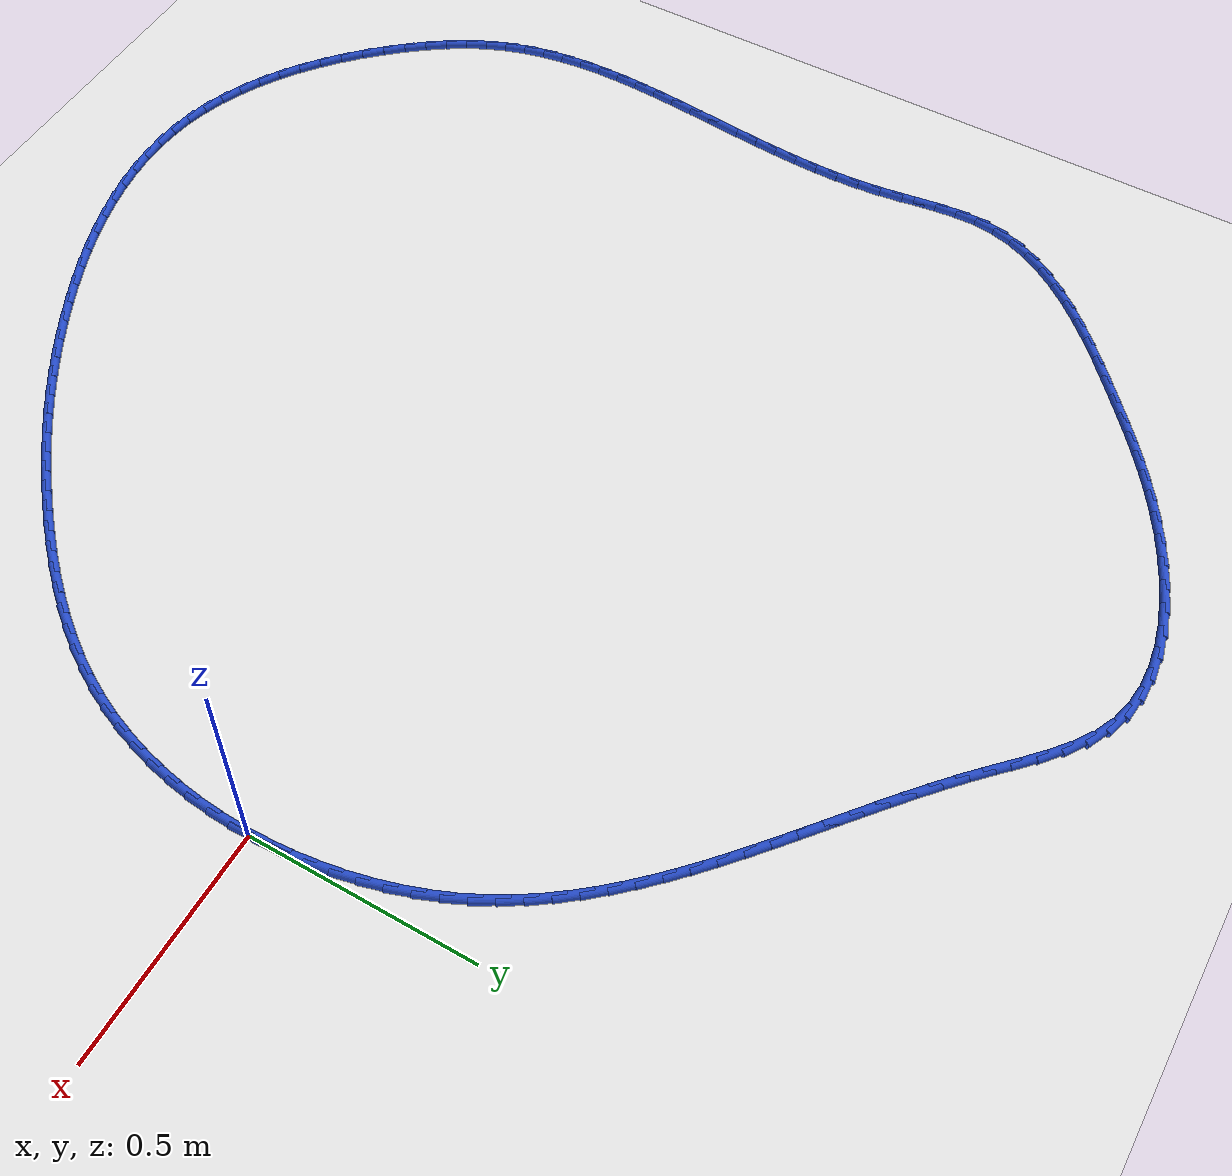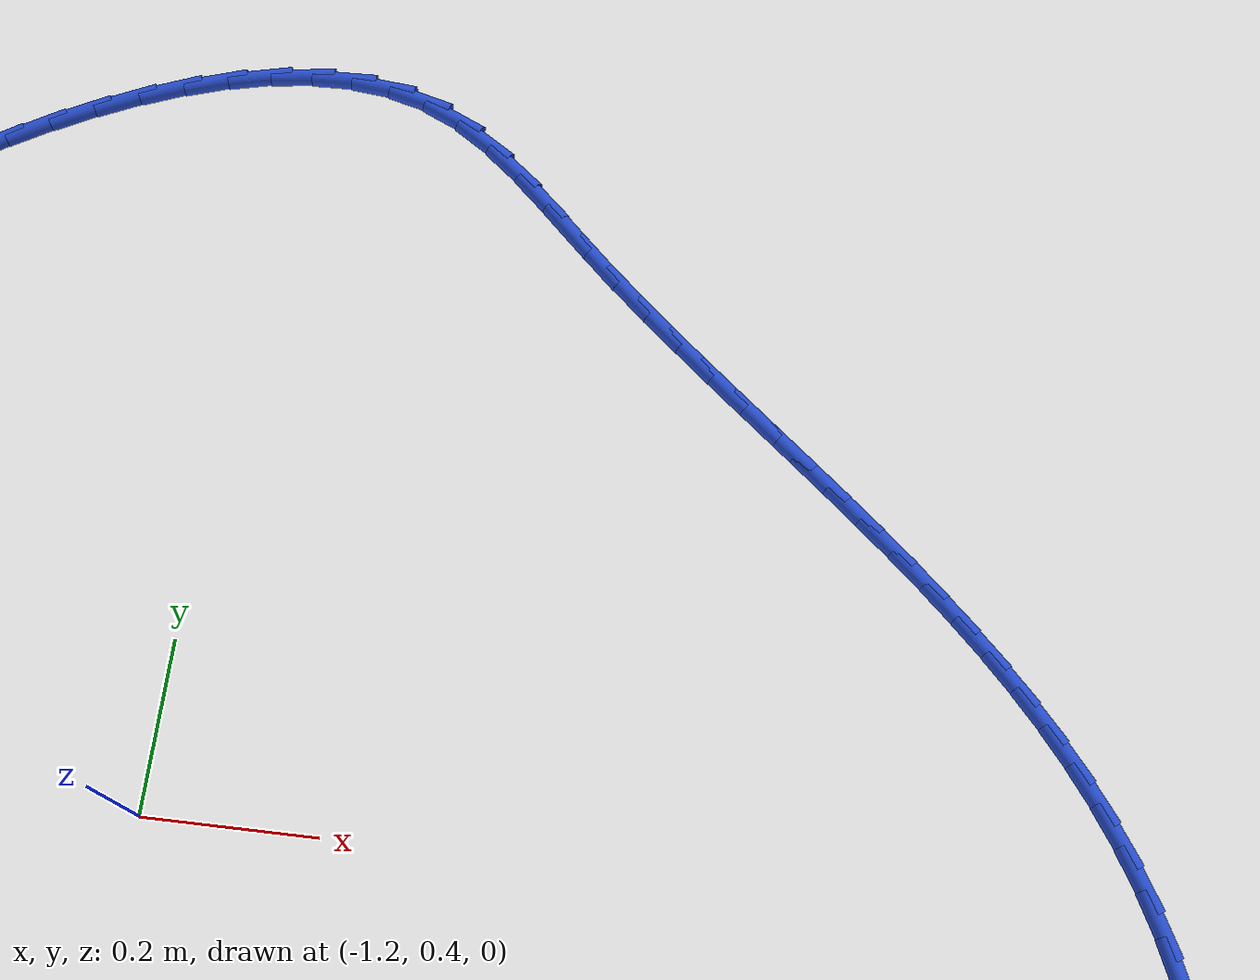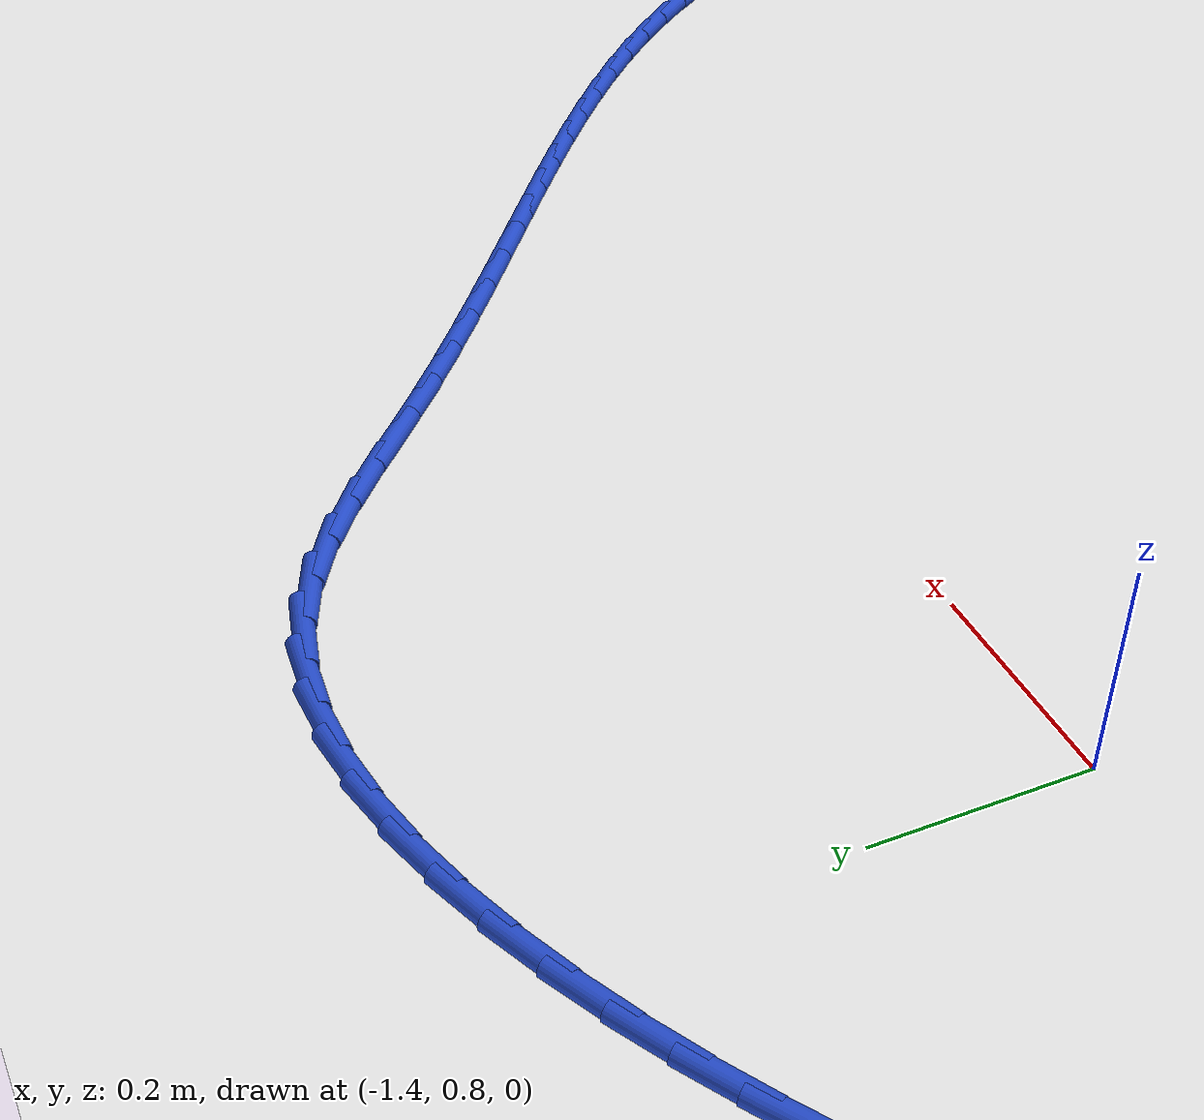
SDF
<sdf version="1.6">
 <world name="default">
  <light name="sun" type="directional">
   <pose>0 0 10 0 -0 0</pose>
   <diffuse>0.8 0.8 0.8 1</diffuse>
   <specular>0.2 0.2 0.2 1</specular>
   <attenuation>
    <range>1000</range>
    <constant>0.9</constant>
    <linear>0.01</linear>
    <quadratic>0.001</quadratic>
   </attenuation>
   <direction>-0.5 0.1 -0.9</direction>
  </light>
  <model name="ground_plane">
   <static>1</static>
   <link name="link">
    <collision name="collision">
     <geometry><plane><normal>0 0 1</normal><size>100 100</size></plane></geometry>
     <surface><friction><ode><mu>100</mu><mu2>50</mu2></ode></friction></surface>
    </collision>
    <visual name="visual">
     <cast_shadows>0</cast_shadows>
     <geometry><plane><normal>0 0 1</normal><size>100 100</size></plane></geometry>
     <material>
      <script><uri>file://media/materials/scripts/gazebo.material</uri><name>Gazebo/WhiteGlow</name></script>
     </material>
    </visual>
   </link>
  </model>
  <gravity>0 0 -9.8</gravity>
  <magnetic_field>6e-06 2.3e-05 -4.2e-05</magnetic_field>
  <atmosphere type="adiabatic"/>
  <physics name="default_physics" default="0" type="ode">
   <max_step_size>0.001</max_step_size>
   <real_time_factor>1</real_time_factor>
   <real_time_update_rate>1000</real_time_update_rate>
  </physics>
  <scene><ambient>0.4 0.4 0.4 1</ambient><background>0.7 0.7 0.7 1</background><shadows>1</shadows></scene>
  <spherical_coordinates>
   <surface_model>EARTH_WGS84</surface_model>
   <latitude_deg>0</latitude_deg>
   <longitude_deg>0</longitude_deg>
   <elevation>0</elevation>
   <heading_deg>0</heading_deg>
  </spherical_coordinates>
  <model name="line">
   <link name="link_0">
    <pose>1.734723475976807e-18 -4.163336342344337e-17 0.01 0 1.57 -1.5426971802619949</pose>
    <collision name="collision">
     <geometry><cylinder><radius>0.01</radius><length>0.08</length></cylinder></geometry>
    </collision>
    <visual name="visual">
     <material>
      <script><name>Gazebo/Blue</name><uri>file://media/materials/scripts/gazebo.material</uri></script>
     </material>
     <geometry><cylinder><radius>0.01</radius><length>0.08</length></cylinder></geometry>
    </visual>
   </link>
   <link name="link_1">
    <pose>-0.0015022339804778787 0.053447836536004205 0.01 0 1.57 -1.4918860255658026</pose>
    <collision name="collision">
     <geometry><cylinder><radius>0.01</radius><length>0.08</length></cylinder></geometry>
    </collision>
    <visual name="visual">
     <material>
      <script><name>Gazebo/Blue</name><uri>file://media/materials/scripts/gazebo.material</uri></script>
     </material>
     <geometry><cylinder><radius>0.01</radius><length>0.08</length></cylinder></geometry>
    </visual>
   </link>
   <link name="link_2">
    <pose>-0.005718462823511615 0.10676754116044428 0.01 0 1.57 -1.4407691615304024</pose>
    <collision name="collision">
     <geometry><cylinder><radius>0.01</radius><length>0.08</length></cylinder></geometry>
    </collision>
    <visual name="visual">
     <material>
      <script><name>Gazebo/Blue</name><uri>file://media/materials/scripts/gazebo.material</uri></script>
     </material>
     <geometry><cylinder><radius>0.01</radius><length>0.08</length></cylinder></geometry>
    </visual>
   </link>
   <link name="link_3">
    <pose>-0.012642421567694281 0.1597171952297842 0.01 0 1.57 -1.3889186938753042</pose>
    <collision name="collision">
     <geometry><cylinder><radius>0.01</radius><length>0.08</length></cylinder></geometry>
    </collision>
    <visual name="visual">
     <material>
      <script><name>Gazebo/Blue</name><uri>file://media/materials/scripts/gazebo.material</uri></script>
     </material>
     <geometry><cylinder><radius>0.01</radius><length>0.08</length></cylinder></geometry>
    </visual>
   </link>
   <link name="link_4">
    <pose>-0.02226784525161897 0.21205488010048779 0.01 0 1.57 -1.335903203767169</pose>
    <collision name="collision">
     <geometry><cylinder><radius>0.01</radius><length>0.08</length></cylinder></geometry>
    </collision>
    <visual name="visual">
     <material>
      <script><name>Gazebo/Blue</name><uri>file://media/materials/scripts/gazebo.material</uri></script>
     </material>
     <geometry><cylinder><radius>0.01</radius><length>0.08</length></cylinder></geometry>
    </visual>
   </link>
   <link name="link_5">
    <pose>-0.03458846891387879 0.2635386771290194 0.01 0 1.57 -1.2812859101356902</pose>
    <collision name="collision">
     <geometry><cylinder><radius>0.01</radius><length>0.08</length></cylinder></geometry>
    </collision>
    <visual name="visual">
     <material>
      <script><name>Gazebo/Blue</name><uri>file://media/materials/scripts/gazebo.material</uri></script>
     </material>
     <geometry><cylinder><radius>0.01</radius><length>0.08</length></cylinder></geometry>
    </visual>
   </link>
   <link name="link_6">
    <pose>-0.049598027593066835 0.3139266676718427 0.01 0 1.57 -1.2246248402349118</pose>
    <collision name="collision">
     <geometry><cylinder><radius>0.01</radius><length>0.08</length></cylinder></geometry>
    </collision>
    <visual name="visual">
     <material>
      <script><name>Gazebo/Blue</name><uri>file://media/materials/scripts/gazebo.material</uri></script>
     </material>
     <geometry><cylinder><radius>0.01</radius><length>0.08</length></cylinder></geometry>
    </visual>
   </link>
   <link name="link_7">
    <pose>-0.06729025632777619 0.36297693308542167 0.01 0 1.57 -1.1654760408640223</pose>
    <collision name="collision">
     <geometry><cylinder><radius>0.01</radius><length>0.08</length></cylinder></geometry>
    </collision>
    <visual name="visual">
     <material>
      <script><name>Gazebo/Blue</name><uri>file://media/materials/scripts/gazebo.material</uri></script>
     </material>
     <geometry><cylinder><radius>0.01</radius><length>0.08</length></cylinder></geometry>
    </visual>
   </link>
   <link name="link_8">
    <pose>-0.08765889015659996 0.4104475547262205 0.01 0 1.57 -1.1035345253752182</pose>
    <collision name="collision">
     <geometry><cylinder><radius>0.01</radius><length>0.08</length></cylinder></geometry>
    </collision>
    <visual name="visual">
     <material>
      <script><name>Gazebo/Blue</name><uri>file://media/materials/scripts/gazebo.material</uri></script>
     </material>
     <geometry><cylinder><radius>0.01</radius><length>0.08</length></cylinder></geometry>
    </visual>
   </link>
   <link name="link_9">
    <pose>-0.11069406333752672 0.45610461890982995 0.01 0 1.57 -1.0417806762022839</pose>
    <collision name="collision">
     <geometry><cylinder><radius>0.01</radius><length>0.08</length></cylinder></geometry>
    </collision>
    <visual name="visual">
     <material>
      <script><name>Gazebo/Blue</name><uri>file://media/materials/scripts/gazebo.material</uri></script>
     </material>
     <geometry><cylinder><radius>0.01</radius><length>0.08</length></cylinder></geometry>
    </visual>
   </link>
   <link name="link_10">
    <pose>-0.13629986348260908 0.49990550377418974 0.01 0 1.57 -0.9839841862624333</pose>
    <collision name="collision">
     <geometry><cylinder><radius>0.01</radius><length>0.08</length></cylinder></geometry>
    </collision>
    <visual name="visual">
     <material>
      <script><name>Gazebo/Blue</name><uri>file://media/materials/scripts/gazebo.material</uri></script>
     </material>
     <geometry><cylinder><radius>0.01</radius><length>0.08</length></cylinder></geometry>
    </visual>
   </link>
   <link name="link_11">
    <pose>-0.16429249867418458 0.542002953995977 0.01 0 1.57 -0.930854958626746</pose>
    <collision name="collision">
     <geometry><cylinder><radius>0.01</radius><length>0.08</length></cylinder></geometry>
    </collision>
    <visual name="visual">
     <material>
      <script><name>Gazebo/Blue</name><uri>file://media/materials/scripts/gazebo.material</uri></script>
     </material>
     <geometry><cylinder><radius>0.01</radius><length>0.08</length></cylinder></geometry>
    </visual>
   </link>
   <link name="link_12">
    <pose>-0.19448420958617776 0.5825585342677677 0.01 0 1.57 -0.8827694725404054</pose>
    <collision name="collision">
     <geometry><cylinder><radius>0.01</radius><length>0.08</length></cylinder></geometry>
    </collision>
    <visual name="visual">
     <material>
      <script><name>Gazebo/Blue</name><uri>file://media/materials/scripts/gazebo.material</uri></script>
     </material>
     <geometry><cylinder><radius>0.01</radius><length>0.08</length></cylinder></geometry>
    </visual>
   </link>
   <link name="link_13">
    <pose>-0.22668723689251352 0.621733809282139 0.01 0 1.57 -0.8399394570988964</pose>
    <collision name="collision">
     <geometry><cylinder><radius>0.01</radius><length>0.08</length></cylinder></geometry>
    </collision>
    <visual name="visual">
     <material>
      <script><name>Gazebo/Blue</name><uri>file://media/materials/scripts/gazebo.material</uri></script>
     </material>
     <geometry><cylinder><radius>0.01</radius><length>0.08</length></cylinder></geometry>
    </visual>
   </link>
   <link name="link_14">
    <pose>-0.26071382126711634 0.6596903437316667 0.01 0 1.57 -0.8024437392678919</pose>
    <collision name="collision">
     <geometry><cylinder><radius>0.01</radius><length>0.08</length></cylinder></geometry>
    </collision>
    <visual name="visual">
     <material>
      <script><name>Gazebo/Blue</name><uri>file://media/materials/scripts/gazebo.material</uri></script>
     </material>
     <geometry><cylinder><radius>0.01</radius><length>0.08</length></cylinder></geometry>
    </visual>
   </link>
   <link name="link_15">
    <pose>-0.2963762033839112 0.6965897023089275 0.01 0 1.57 -0.7702630854326</pose>
    <collision name="collision">
     <geometry><cylinder><radius>0.01</radius><length>0.08</length></cylinder></geometry>
    </collision>
    <visual name="visual">
     <material>
      <script><name>Gazebo/Blue</name><uri>file://media/materials/scripts/gazebo.material</uri></script>
     </material>
     <geometry><cylinder><radius>0.01</radius><length>0.08</length></cylinder></geometry>
    </visual>
   </link>
   <link name="link_16">
    <pose>-0.33348662391682266 0.7325934497064981 0.01 0 1.57 -0.7433130078955876</pose>
    <collision name="collision">
     <geometry><cylinder><radius>0.01</radius><length>0.08</length></cylinder></geometry>
    </collision>
    <visual name="visual">
     <material>
      <script><name>Gazebo/Blue</name><uri>file://media/materials/scripts/gazebo.material</uri></script>
     </material>
     <geometry><cylinder><radius>0.01</radius><length>0.08</length></cylinder></geometry>
    </visual>
   </link>
   <link name="link_17">
    <pose>-0.37185732353977546 0.7678631506169545 0.01 0 1.57 -0.721471733752869</pose>
    <collision name="collision">
     <geometry><cylinder><radius>0.01</radius><length>0.08</length></cylinder></geometry>
    </collision>
    <visual name="visual">
     <material>
      <script><name>Gazebo/Blue</name><uri>file://media/materials/scripts/gazebo.material</uri></script>
     </material>
     <geometry><cylinder><radius>0.01</radius><length>0.08</length></cylinder></geometry>
    </visual>
   </link>
   <link name="link_18">
    <pose>-0.4113005429266942 0.8025603697328734 0.01 0 1.57 -0.7046022982739107</pose>
    <collision name="collision">
     <geometry><cylinder><radius>0.01</radius><length>0.08</length></cylinder></geometry>
    </collision>
    <visual name="visual">
     <material>
      <script><name>Gazebo/Blue</name><uri>file://media/materials/scripts/gazebo.material</uri></script>
     </material>
     <geometry><cylinder><radius>0.01</radius><length>0.08</length></cylinder></geometry>
    </visual>
   </link>
   <link name="link_19">
    <pose>-0.45162852275150395 0.8368466717468315 0.01 0 1.57 -0.6925688538961021</pose>
    <collision name="collision">
     <geometry><cylinder><radius>0.01</radius><length>0.08</length></cylinder></geometry>
    </collision>
    <visual name="visual">
     <material>
      <script><name>Gazebo/Blue</name><uri>file://media/materials/scripts/gazebo.material</uri></script>
     </material>
     <geometry><cylinder><radius>0.01</radius><length>0.08</length></cylinder></geometry>
    </visual>
   </link>
   <link name="link_20">
    <pose>-0.49265350368812916 0.8708836213514047 0.01 0 1.57 -0.6852478548191504</pose>
    <collision name="collision">
     <geometry><cylinder><radius>0.01</radius><length>0.08</length></cylinder></geometry>
    </collision>
    <visual name="visual">
     <material>
      <script><name>Gazebo/Blue</name><uri>file://media/materials/scripts/gazebo.material</uri></script>
     </material>
     <geometry><cylinder><radius>0.01</radius><length>0.08</length></cylinder></geometry>
    </visual>
   </link>
   <link name="link_21">
    <pose>-0.5341877264104945 0.9048327832391699 0.01 0 1.57 -0.6825349512254969</pose>
    <collision name="collision">
     <geometry><cylinder><radius>0.01</radius><length>0.08</length></cylinder></geometry>
    </collision>
    <visual name="visual">
     <material>
      <script><name>Gazebo/Blue</name><uri>file://media/materials/scripts/gazebo.material</uri></script>
     </material>
     <geometry><cylinder><radius>0.01</radius><length>0.08</length></cylinder></geometry>
    </visual>
   </link>
   <link name="link_22">
    <pose>-0.5760434315925248 0.9388557221027034 0.01 0 1.57 -0.6843483671279676</pose>
    <collision name="collision">
     <geometry><cylinder><radius>0.01</radius><length>0.08</length></cylinder></geometry>
    </collision>
    <visual name="visual">
     <material>
      <script><name>Gazebo/Blue</name><uri>file://media/materials/scripts/gazebo.material</uri></script>
     </material>
     <geometry><cylinder><radius>0.01</radius><length>0.08</length></cylinder></geometry>
    </visual>
   </link>
   <link name="link_23">
    <pose>-0.6180328599081448 0.9731140026345817 0.01 0 1.57 -0.6906293621919062</pose>
    <collision name="collision">
     <geometry><cylinder><radius>0.01</radius><length>0.08</length></cylinder></geometry>
    </collision>
    <visual name="visual">
     <material>
      <script><name>Gazebo/Blue</name><uri>file://media/materials/scripts/gazebo.material</uri></script>
     </material>
     <geometry><cylinder><radius>0.01</radius><length>0.08</length></cylinder></geometry>
    </visual>
   </link>
   <link name="link_24">
    <pose>-0.6599682520312792 1.007769189527381 0.01 0 1.57 -0.7013401686845019</pose>
    <collision name="collision">
     <geometry><cylinder><radius>0.01</radius><length>0.08</length></cylinder></geometry>
    </collision>
    <visual name="visual">
     <material>
      <script><name>Gazebo/Blue</name><uri>file://media/materials/scripts/gazebo.material</uri></script>
     </material>
     <geometry><cylinder><radius>0.01</radius><length>0.08</length></cylinder></geometry>
    </visual>
   </link>
   <link name="link_25">
    <pose>-0.7016618486358527 1.0429828474736784 0.01 0 1.57 -0.716459597336924</pose>
    <collision name="collision">
     <geometry><cylinder><radius>0.01</radius><length>0.08</length></cylinder></geometry>
    </collision>
    <visual name="visual">
     <material>
      <script><name>Gazebo/Blue</name><uri>file://media/materials/scripts/gazebo.material</uri></script>
     </material>
     <geometry><cylinder><radius>0.01</radius><length>0.08</length></cylinder></geometry>
    </visual>
   </link>
   <link name="link_26">
    <pose>-0.7429258903957899 1.0789165411660497 0.01 0 1.57 -0.7359763510065386</pose>
    <collision name="collision">
     <geometry><cylinder><radius>0.01</radius><length>0.08</length></cylinder></geometry>
    </collision>
    <visual name="visual">
     <material>
      <script><name>Gazebo/Blue</name><uri>file://media/materials/scripts/gazebo.material</uri></script>
     </material>
     <geometry><cylinder><radius>0.01</radius><length>0.08</length></cylinder></geometry>
    </visual>
   </link>
   <link name="link_27">
    <pose>-0.7835726179850158 1.1157318352970718 0.01 0 1.57 -0.758681382193256</pose>
    <collision name="collision">
     <geometry><cylinder><radius>0.01</radius><length>0.08</length></cylinder></geometry>
    </collision>
    <visual name="visual">
     <material>
      <script><name>Gazebo/Blue</name><uri>file://media/materials/scripts/gazebo.material</uri></script>
     </material>
     <geometry><cylinder><radius>0.01</radius><length>0.08</length></cylinder></geometry>
    </visual>
   </link>
   <link name="link_28">
    <pose>-0.8234443561158281 1.1535280420847367 0.01 0 1.57 -0.7650895219617803</pose>
    <collision name="collision">
     <geometry><cylinder><radius>0.01</radius><length>0.08</length></cylinder></geometry>
    </collision>
    <visual name="visual">
     <material>
      <script><name>Gazebo/Blue</name><uri>file://media/materials/scripts/gazebo.material</uri></script>
     </material>
     <geometry><cylinder><radius>0.01</radius><length>0.08</length></cylinder></geometry>
    </visual>
   </link>
   <link name="link_29">
    <pose>-0.8628745005210463 1.1913883074383602 0.01 0 1.57 -0.7387590862731238</pose>
    <collision name="collision">
     <geometry><cylinder><radius>0.01</radius><length>0.08</length></cylinder></geometry>
    </collision>
    <visual name="visual">
     <material>
      <script><name>Gazebo/Blue</name><uri>file://media/materials/scripts/gazebo.material</uri></script>
     </material>
     <geometry><cylinder><radius>0.01</radius><length>0.08</length></cylinder></geometry>
    </visual>
   </link>
   <link name="link_30">
    <pose>-0.9025965634298801 1.2275678218673516 0.01 0 1.57 -0.6765711795817975</pose>
    <collision name="collision">
     <geometry><cylinder><radius>0.01</radius><length>0.08</length></cylinder></geometry>
    </collision>
    <visual name="visual">
     <material>
      <script><name>Gazebo/Blue</name><uri>file://media/materials/scripts/gazebo.material</uri></script>
     </material>
     <geometry><cylinder><radius>0.01</radius><length>0.08</length></cylinder></geometry>
    </visual>
   </link>
   <link name="link_31">
    <pose>-0.9433557106158903 1.2602976613668213 0.01 0 1.57 -0.5740472039964976</pose>
    <collision name="collision">
     <geometry><cylinder><radius>0.01</radius><length>0.08</length></cylinder></geometry>
    </collision>
    <visual name="visual">
     <material>
      <script><name>Gazebo/Blue</name><uri>file://media/materials/scripts/gazebo.material</uri></script>
     </material>
     <geometry><cylinder><radius>0.01</radius><length>0.08</length></cylinder></geometry>
    </visual>
   </link>
   <link name="link_32">
    <pose>-0.9858971078526381 1.287808901931881 0.01 0 1.57 -0.4274919909227677</pose>
    <collision name="collision">
     <geometry><cylinder><radius>0.01</radius><length>0.08</length></cylinder></geometry>
    </collision>
    <visual name="visual">
     <material>
      <script><name>Gazebo/Blue</name><uri>file://media/materials/scripts/gazebo.material</uri></script>
     </material>
     <geometry><cylinder><radius>0.01</radius><length>0.08</length></cylinder></geometry>
    </visual>
   </link>
   <link name="link_33">
    <pose>-1.0309619772264824 1.3083399597093148 0.01 0 1.57 -0.257097699735833</pose>
    <collision name="collision">
     <geometry><cylinder><radius>0.01</radius><length>0.08</length></cylinder></geometry>
    </collision>
    <visual name="visual">
     <material>
      <script><name>Gazebo/Blue</name><uri>file://media/materials/scripts/gazebo.material</uri></script>
     </material>
     <geometry><cylinder><radius>0.01</radius><length>0.08</length></cylinder></geometry>
    </visual>
   </link>
   <link name="link_34">
    <pose>-1.0788596819454515 1.3209330442270673 0.01 0 1.57 -0.10346244114178764</pose>
    <collision name="collision">
     <geometry><cylinder><radius>0.01</radius><length>0.08</length></cylinder></geometry>
    </collision>
    <visual name="visual">
     <material>
      <script><name>Gazebo/Blue</name><uri>file://media/materials/scripts/gazebo.material</uri></script>
     </material>
     <geometry><cylinder><radius>0.01</radius><length>0.08</length></cylinder></geometry>
    </visual>
   </link>
   <link name="link_35">
    <pose>-1.1290841881260079 1.3261480153801308 0.01 0 1.57 0.0276098296760891</pose>
    <collision name="collision">
     <geometry><cylinder><radius>0.01</radius><length>0.08</length></cylinder></geometry>
    </collision>
    <visual name="visual">
     <material>
      <script><name>Gazebo/Blue</name><uri>file://media/materials/scripts/gazebo.material</uri></script>
     </material>
     <geometry><cylinder><radius>0.01</radius><length>0.08</length></cylinder></geometry>
    </visual>
   </link>
   <link name="link_36">
    <pose>-1.1810389548182976 1.3247131885115697 0.01 0 1.57 0.13769016228136968</pose>
    <collision name="collision">
     <geometry><cylinder><radius>0.01</radius><length>0.08</length></cylinder></geometry>
    </collision>
    <visual name="visual">
     <material>
      <script><name>Gazebo/Blue</name><uri>file://media/materials/scripts/gazebo.material</uri></script>
     </material>
     <geometry><cylinder><radius>0.01</radius><length>0.08</length></cylinder></geometry>
    </visual>
   </link>
   <link name="link_37">
    <pose>-1.2341274410724663 1.3173568789644485 0.01 0 1.57 0.22988302466952343</pose>
    <collision name="collision">
     <geometry><cylinder><radius>0.01</radius><length>0.08</length></cylinder></geometry>
    </collision>
    <visual name="visual">
     <material>
      <script><name>Gazebo/Blue</name><uri>file://media/materials/scripts/gazebo.material</uri></script>
     </material>
     <geometry><cylinder><radius>0.01</radius><length>0.08</length></cylinder></geometry>
    </visual>
   </link>
   <link name="link_38">
    <pose>-1.28775310593866 1.304807402081832 0.01 0 1.57 0.30755270170980087</pose>
    <collision name="collision">
     <geometry><cylinder><radius>0.01</radius><length>0.08</length></cylinder></geometry>
    </collision>
    <visual name="visual">
     <material>
      <script><name>Gazebo/Blue</name><uri>file://media/materials/scripts/gazebo.material</uri></script>
     </material>
     <geometry><cylinder><radius>0.01</radius><length>0.08</length></cylinder></geometry>
    </visual>
   </link>
   <link name="link_39">
    <pose>-1.341319408467025 1.2877930732067853 0.01 0 1.57 0.37375449248183745</pose>
    <collision name="collision">
     <geometry><cylinder><radius>0.01</radius><length>0.08</length></cylinder></geometry>
    </collision>
    <visual name="visual">
     <material>
      <script><name>Gazebo/Blue</name><uri>file://media/materials/scripts/gazebo.material</uri></script>
     </material>
     <geometry><cylinder><radius>0.01</radius><length>0.08</length></cylinder></geometry>
    </visual>
   </link>
   <link name="link_40">
    <pose>-1.3942298077077069 1.2670422076823724 0.01 0 1.57 0.4310816607656567</pose>
    <collision name="collision">
     <geometry><cylinder><radius>0.01</radius><length>0.08</length></cylinder></geometry>
    </collision>
    <visual name="visual">
     <material>
      <script><name>Gazebo/Blue</name><uri>file://media/materials/scripts/gazebo.material</uri></script>
     </material>
     <geometry><cylinder><radius>0.01</radius><length>0.08</length></cylinder></geometry>
    </visual>
   </link>
   <link name="link_41">
    <pose>-1.4458877627108517 1.2432831208516586 0.01 0 1.57 0.4817028739370108</pose>
    <collision name="collision">
     <geometry><cylinder><radius>0.01</radius><length>0.08</length></cylinder></geometry>
    </collision>
    <visual name="visual">
     <material>
      <script><name>Gazebo/Blue</name><uri>file://media/materials/scripts/gazebo.material</uri></script>
     </material>
     <geometry><cylinder><radius>0.01</radius><length>0.08</length></cylinder></geometry>
    </visual>
   </link>
   <link name="link_42">
    <pose>-1.4956967325266044 1.217244128057708 0.01 0 1.57 0.52747608561577</pose>
    <collision name="collision">
     <geometry><cylinder><radius>0.01</radius><length>0.08</length></cylinder></geometry>
    </collision>
    <visual name="visual">
     <material>
      <script><name>Gazebo/Blue</name><uri>file://media/materials/scripts/gazebo.material</uri></script>
     </material>
     <geometry><cylinder><radius>0.01</radius><length>0.08</length></cylinder></geometry>
    </visual>
   </link>
   <link name="link_43">
    <pose>-1.5430642402255068 1.1896510560826425 0.01 0 1.57 0.5698921180799426</pose>
    <collision name="collision">
     <geometry><cylinder><radius>0.01</radius><length>0.08</length></cylinder></geometry>
    </collision>
    <visual name="visual">
     <material>
      <script><name>Gazebo/Blue</name><uri>file://media/materials/scripts/gazebo.material</uri></script>
     </material>
     <geometry><cylinder><radius>0.01</radius><length>0.08</length></cylinder></geometry>
    </visual>
   </link>
   <link name="link_44">
    <pose>-1.5878068583820595 1.1609792544667137 0.01 0 1.57 0.6084445797164493</pose>
    <collision name="collision">
     <geometry><cylinder><radius>0.01</radius><length>0.08</length></cylinder></geometry>
    </collision>
    <visual name="visual">
     <material>
      <script><name>Gazebo/Blue</name><uri>file://media/materials/scripts/gazebo.material</uri></script>
     </material>
     <geometry><cylinder><radius>0.01</radius><length>0.08</length></cylinder></geometry>
    </visual>
   </link>
   <link name="link_45">
    <pose>-1.6304945977595184 1.131242712651671 0.01 0 1.57 0.6415445420107869</pose>
    <collision name="collision">
     <geometry><cylinder><radius>0.01</radius><length>0.08</length></cylinder></geometry>
    </collision>
    <visual name="visual">
     <material>
      <script><name>Gazebo/Blue</name><uri>file://media/materials/scripts/gazebo.material</uri></script>
     </material>
     <geometry><cylinder><radius>0.01</radius><length>0.08</length></cylinder></geometry>
    </visual>
   </link>
   <link name="link_46">
    <pose>-1.6717785745057814 1.100405756034084 0.01 0 1.57 0.6679036598819538</pose>
    <collision name="collision">
     <geometry><cylinder><radius>0.01</radius><length>0.08</length></cylinder></geometry>
    </collision>
    <visual name="visual">
     <material>
      <script><name>Gazebo/Blue</name><uri>file://media/materials/scripts/gazebo.material</uri></script>
     </material>
     <geometry><cylinder><radius>0.01</radius><length>0.08</length></cylinder></geometry>
    </visual>
   </link>
   <link name="link_47">
    <pose>-1.7123099047687471 1.0684327100105226 0.01 0 1.57 0.6867048547310521</pose>
    <collision name="collision">
     <geometry><cylinder><radius>0.01</radius><length>0.08</length></cylinder></geometry>
    </collision>
    <visual name="visual">
     <material>
      <script><name>Gazebo/Blue</name><uri>file://media/materials/scripts/gazebo.material</uri></script>
     </material>
     <geometry><cylinder><radius>0.01</radius><length>0.08</length></cylinder></geometry>
    </visual>
   </link>
   <link name="link_48">
    <pose>-1.752739704696312 1.0352878999775552 0.01 0 1.57 0.6976746352785685</pose>
    <collision name="collision">
     <geometry><cylinder><radius>0.01</radius><length>0.08</length></cylinder></geometry>
    </collision>
    <visual name="visual">
     <material>
      <script><name>Gazebo/Blue</name><uri>file://media/materials/scripts/gazebo.material</uri></script>
     </material>
     <geometry><cylinder><radius>0.01</radius><length>0.08</length></cylinder></geometry>
    </visual>
   </link>
   <link name="link_49">
    <pose>-1.7937171312119102 1.0009356607639786 0.01 0 1.57 0.7059096828283525</pose>
    <collision name="collision">
     <geometry><cylinder><radius>0.01</radius><length>0.08</length></cylinder></geometry>
    </collision>
    <visual name="visual">
     <material>
      <script><name>Gazebo/Blue</name><uri>file://media/materials/scripts/gazebo.material</uri></script>
     </material>
     <geometry><cylinder><radius>0.01</radius><length>0.08</length></cylinder></geometry>
    </visual>
   </link>
   <link name="link_50">
    <pose>-1.8354716913148823 0.9653423475045981 0.01 0 1.57 0.7224555286427939</pose>
    <collision name="collision">
     <geometry><cylinder><radius>0.01</radius><length>0.08</length></cylinder></geometry>
    </collision>
    <visual name="visual">
     <material>
      <script><name>Gazebo/Blue</name><uri>file://media/materials/scripts/gazebo.material</uri></script>
     </material>
     <geometry><cylinder><radius>0.01</radius><length>0.08</length></cylinder></geometry>
    </visual>
   </link>
   <link name="link_51">
    <pose>-1.8772944798536975 0.9284788330991479 0.01 0 1.57 0.7488997618551532</pose>
    <collision name="collision">
     <geometry><cylinder><radius>0.01</radius><length>0.08</length></cylinder></geometry>
    </collision>
    <visual name="visual">
     <material>
      <script><name>Gazebo/Blue</name><uri>file://media/materials/scripts/gazebo.material</uri></script>
     </material>
     <geometry><cylinder><radius>0.01</radius><length>0.08</length></cylinder></geometry>
    </visual>
   </link>
   <link name="link_52">
    <pose>-1.9183492895013576 0.8903166033137899 0.01 0 1.57 0.7858901310401349</pose>
    <collision name="collision">
     <geometry><cylinder><radius>0.01</radius><length>0.08</length></cylinder></geometry>
    </collision>
    <visual name="visual">
     <material>
      <script><name>Gazebo/Blue</name><uri>file://media/materials/scripts/gazebo.material</uri></script>
     </material>
     <geometry><cylinder><radius>0.01</radius><length>0.08</length></cylinder></geometry>
    </visual>
   </link>
   <link name="link_53">
    <pose>-1.9577999129308645 0.8508271439146872 0.01 0 1.57 0.8346160034411199</pose>
    <collision name="collision">
     <geometry><cylinder><radius>0.01</radius><length>0.08</length></cylinder></geometry>
    </collision>
    <visual name="visual">
     <material>
      <script><name>Gazebo/Blue</name><uri>file://media/materials/scripts/gazebo.material</uri></script>
     </material>
     <geometry><cylinder><radius>0.01</radius><length>0.08</length></cylinder></geometry>
    </visual>
   </link>
   <link name="link_54">
    <pose>-1.994810142815219 0.8099819406680011 0.01 0 1.57 0.8967768908501994</pose>
    <collision name="collision">
     <geometry><cylinder><radius>0.01</radius><length>0.08</length></cylinder></geometry>
    </collision>
    <visual name="visual">
     <material>
      <script><name>Gazebo/Blue</name><uri>file://media/materials/scripts/gazebo.material</uri></script>
     </material>
     <geometry><cylinder><radius>0.01</radius><length>0.08</length></cylinder></geometry>
    </visual>
   </link>
   <link name="link_55">
    <pose>-2.0285437718274246 0.7677524793398948 0.01 0 1.57 0.974496028083345</pose>
    <collision name="collision">
     <geometry><cylinder><radius>0.01</radius><length>0.08</length></cylinder></geometry>
    </collision>
    <visual name="visual">
     <material>
      <script><name>Gazebo/Blue</name><uri>file://media/materials/scripts/gazebo.material</uri></script>
     </material>
     <geometry><cylinder><radius>0.01</radius><length>0.08</length></cylinder></geometry>
    </visual>
   </link>
   <link name="link_56">
    <pose>-2.058164592640482 0.7241102456965307 0.01 0 1.57 1.0700694714820989</pose>
    <collision name="collision">
     <geometry><cylinder><radius>0.01</radius><length>0.08</length></cylinder></geometry>
    </collision>
    <visual name="visual">
     <material>
      <script><name>Gazebo/Blue</name><uri>file://media/materials/scripts/gazebo.material</uri></script>
     </material>
     <geometry><cylinder><radius>0.01</radius><length>0.08</length></cylinder></geometry>
    </visual>
   </link>
   <link name="link_57">
    <pose>-2.0828363979273945 0.6790267255040703 0.01 0 1.57 1.1853876774774041</pose>
    <collision name="collision">
     <geometry><cylinder><radius>0.01</radius><length>0.08</length></cylinder></geometry>
    </collision>
    <visual name="visual">
     <material>
      <script><name>Gazebo/Blue</name><uri>file://media/materials/scripts/gazebo.material</uri></script>
     </material>
     <geometry><cylinder><radius>0.01</radius><length>0.08</length></cylinder></geometry>
    </visual>
   </link>
   <link name="link_58">
    <pose>-2.1017229803611612 0.6324734045286766 0.01 0 1.57 1.3208831673454786</pose>
    <collision name="collision">
     <geometry><cylinder><radius>0.01</radius><length>0.08</length></cylinder></geometry>
    </collision>
    <visual name="visual">
     <material>
      <script><name>Gazebo/Blue</name><uri>file://media/materials/scripts/gazebo.material</uri></script>
     </material>
     <geometry><cylinder><radius>0.01</radius><length>0.08</length></cylinder></geometry>
    </visual>
   </link>
   <link name="link_59">
    <pose>-2.1139881326147862 0.5844217685365118 0.01 0 1.57 1.4704897507283414</pose>
    <collision name="collision">
     <geometry><cylinder><radius>0.01</radius><length>0.08</length></cylinder></geometry>
    </collision>
    <visual name="visual">
     <material>
      <script><name>Gazebo/Blue</name><uri>file://media/materials/scripts/gazebo.material</uri></script>
     </material>
     <geometry><cylinder><radius>0.01</radius><length>0.08</length></cylinder></geometry>
    </visual>
   </link>
   <link name="link_60">
    <pose>-2.118976255375132 0.5348598899255452 0.01 0 1.57 -1.5469745737501712</pose>
    <collision name="collision">
     <geometry><cylinder><radius>0.01</radius><length>0.08</length></cylinder></geometry>
    </collision>
    <visual name="visual">
     <material>
      <script><name>Gazebo/Blue</name><uri>file://media/materials/scripts/gazebo.material</uri></script>
     </material>
     <geometry><cylinder><radius>0.01</radius><length>0.08</length></cylinder></geometry>
    </visual>
   </link>
   <link name="link_61">
    <pose>-2.1177629015582813 0.4839348262019541 0.01 0 1.57 -1.4678885311835486</pose>
    <collision name="collision">
     <geometry><cylinder><radius>0.01</radius><length>0.08</length></cylinder></geometry>
    </collision>
    <visual name="visual">
     <material>
      <script><name>Gazebo/Blue</name><uri>file://media/materials/scripts/gazebo.material</uri></script>
     </material>
     <geometry><cylinder><radius>0.01</radius><length>0.08</length></cylinder></geometry>
    </visual>
   </link>
   <link name="link_62">
    <pose>-2.1123872845141194 0.43188213526821945 0.01 0 1.57 -1.4302901974698563</pose>
    <collision name="collision">
     <geometry><cylinder><radius>0.01</radius><length>0.08</length></cylinder></geometry>
    </collision>
    <visual name="visual">
     <material>
      <script><name>Gazebo/Blue</name><uri>file://media/materials/scripts/gazebo.material</uri></script>
     </material>
     <geometry><cylinder><radius>0.01</radius><length>0.08</length></cylinder></geometry>
    </visual>
   </link>
   <link name="link_63">
    <pose>-2.104899012588457 0.37893832967975283 0.01 0 1.57 -1.4308305498377138</pose>
    <collision name="collision">
     <geometry><cylinder><radius>0.01</radius><length>0.08</length></cylinder></geometry>
    </collision>
    <visual name="visual">
     <material>
      <script><name>Gazebo/Blue</name><uri>file://media/materials/scripts/gazebo.material</uri></script>
     </material>
     <geometry><cylinder><radius>0.01</radius><length>0.08</length></cylinder></geometry>
    </visual>
   </link>
   <link name="link_64">
    <pose>-2.097347694127105 0.32533992199196765 0.01 0 1.57 -1.4667395222645625</pose>
    <collision name="collision">
     <geometry><cylinder><radius>0.01</radius><length>0.08</length></cylinder></geometry>
    </collision>
    <visual name="visual">
     <material>
      <script><name>Gazebo/Blue</name><uri>file://media/materials/scripts/gazebo.material</uri></script>
     </material>
     <geometry><cylinder><radius>0.01</radius><length>0.08</length></cylinder></geometry>
    </visual>
   </link>
   <link name="link_65">
    <pose>-2.0917059792958397 0.2713181052111751 0.01 0 1.57 -1.5151887445399628</pose>
    <collision name="collision">
     <geometry><cylinder><radius>0.01</radius><length>0.08</length></cylinder></geometry>
    </collision>
    <visual name="visual">
     <material>
      <script><name>Gazebo/Blue</name><uri>file://media/materials/scripts/gazebo.material</uri></script>
     </material>
     <geometry><cylinder><radius>0.01</radius><length>0.08</length></cylinder></geometry>
    </visual>
   </link>
   <link name="link_66">
    <pose>-2.0886832962806308 0.21701675516253743 0.01 0 1.57 -1.5574569964108615</pose>
    <collision name="collision">
     <geometry><cylinder><radius>0.01</radius><length>0.08</length></cylinder></geometry>
    </collision>
    <visual name="visual">
     <material>
      <script><name>Gazebo/Blue</name><uri>file://media/materials/scripts/gazebo.material</uri></script>
     </material>
     <geometry><cylinder><radius>0.01</radius><length>0.08</length></cylinder></geometry>
    </visual>
   </link>
   <link name="link_67">
    <pose>-2.0879561475147144 0.16250834916287552 0.01 0 1.57 1.5485733796666912</pose>
    <collision name="collision">
     <geometry><cylinder><radius>0.01</radius><length>0.08</length></cylinder></geometry>
    </collision>
    <visual name="visual">
     <material>
      <script><name>Gazebo/Blue</name><uri>file://media/materials/scripts/gazebo.material</uri></script>
     </material>
     <geometry><cylinder><radius>0.01</radius><length>0.08</length></cylinder></geometry>
    </visual>
   </link>
   <link name="link_68">
    <pose>-2.0891707221871845 0.10786326919891359 0.01 0 1.57 1.519617933913791</pose>
    <collision name="collision">
     <geometry><cylinder><radius>0.01</radius><length>0.08</length></cylinder></geometry>
    </collision>
    <visual name="visual">
     <material>
      <script><name>Gazebo/Blue</name><uri>file://media/materials/scripts/gazebo.material</uri></script>
     </material>
     <geometry><cylinder><radius>0.01</radius><length>0.08</length></cylinder></geometry>
    </visual>
   </link>
   <link name="link_69">
    <pose>-2.0919732094871315 0.05315189725737806 0.01 0 1.57 1.4971445678776278</pose>
    <collision name="collision">
     <geometry><cylinder><radius>0.01</radius><length>0.08</length></cylinder></geometry>
    </collision>
    <visual name="visual">
     <material>
      <script><name>Gazebo/Blue</name><uri>file://media/materials/scripts/gazebo.material</uri></script>
     </material>
     <geometry><cylinder><radius>0.01</radius><length>0.08</length></cylinder></geometry>
    </visual>
   </link>
   <link name="link_70">
    <pose>-2.0960097986036486 -0.001555384675006691 0.01 0 1.57 1.4810394739244146</pose>
    <collision name="collision">
     <geometry><cylinder><radius>0.01</radius><length>0.08</length></cylinder></geometry>
    </collision>
    <visual name="visual">
     <material>
      <script><name>Gazebo/Blue</name><uri>file://media/materials/scripts/gazebo.material</uri></script>
     </material>
     <geometry><cylinder><radius>0.01</radius><length>0.08</length></cylinder></geometry>
    </visual>
   </link>
   <link name="link_71">
    <pose>-2.1009266787258296 -0.05618819461151432 0.01 0 1.57 1.471226439560285</pose>
    <collision name="collision">
     <geometry><cylinder><radius>0.01</radius><length>0.08</length></cylinder></geometry>
    </collision>
    <visual name="visual">
     <material>
      <script><name>Gazebo/Blue</name><uri>file://media/materials/scripts/gazebo.material</uri></script>
     </material>
     <geometry><cylinder><radius>0.01</radius><length>0.08</length></cylinder></geometry>
    </visual>
   </link>
   <link name="link_72">
    <pose>-2.106370039042766 -0.11067615056541998 0.01 0 1.57 1.4676853603187638</pose>
    <collision name="collision">
     <geometry><cylinder><radius>0.01</radius><length>0.08</length></cylinder></geometry>
    </collision>
    <visual name="visual">
     <material>
      <script><name>Gazebo/Blue</name><uri>file://media/materials/scripts/gazebo.material</uri></script>
     </material>
     <geometry><cylinder><radius>0.01</radius><length>0.08</length></cylinder></geometry>
    </visual>
   </link>
   <link name="link_73">
    <pose>-2.1119860687435508 -0.164948870549999 0.01 0 1.57 1.4704642289788816</pose>
    <collision name="collision">
     <geometry><cylinder><radius>0.01</radius><length>0.08</length></cylinder></geometry>
    </collision>
    <visual name="visual">
     <material>
      <script><name>Gazebo/Blue</name><uri>file://media/materials/scripts/gazebo.material</uri></script>
     </material>
     <geometry><cylinder><radius>0.01</radius><length>0.08</length></cylinder></geometry>
    </visual>
   </link>
   <link name="link_74">
    <pose>-2.117420957017276 -0.2189359725785244 0.01 0 1.57 1.4796855732080632</pose>
    <collision name="collision">
     <geometry><cylinder><radius>0.01</radius><length>0.08</length></cylinder></geometry>
    </collision>
    <visual name="visual">
     <material>
      <script><name>Gazebo/Blue</name><uri>file://media/materials/scripts/gazebo.material</uri></script>
     </material>
     <geometry><cylinder><radius>0.01</radius><length>0.08</length></cylinder></geometry>
    </visual>
   </link>
   <link name="link_75">
    <pose>-2.122320893053035 -0.27256707466427166 0.01 0 1.57 1.495547379804677</pose>
    <collision name="collision">
     <geometry><cylinder><radius>0.01</radius><length>0.08</length></cylinder></geometry>
    </collision>
    <visual name="visual">
     <material>
      <script><name>Gazebo/Blue</name><uri>file://media/materials/scripts/gazebo.material</uri></script>
     </material>
     <geometry><cylinder><radius>0.01</radius><length>0.08</length></cylinder></geometry>
    </visual>
   </link>
   <link name="link_76">
    <pose>-2.126332066039919 -0.3257717948205154 0.01 0 1.57 1.518317398589834</pose>
    <collision name="collision">
     <geometry><cylinder><radius>0.01</radius><length>0.08</length></cylinder></geometry>
    </collision>
    <visual name="visual">
     <material>
      <script><name>Gazebo/Blue</name><uri>file://media/materials/scripts/gazebo.material</uri></script>
     </material>
     <geometry><cylinder><radius>0.01</radius><length>0.08</length></cylinder></geometry>
    </visual>
   </link>
   <link name="link_77">
    <pose>-2.129100665167023 -0.3784797510605303 0.01 0 1.57 1.5483184055845474</pose>
    <collision name="collision">
     <geometry><cylinder><radius>0.01</radius><length>0.08</length></cylinder></geometry>
    </collision>
    <visual name="visual">
     <material>
      <script><name>Gazebo/Blue</name><uri>file://media/materials/scripts/gazebo.material</uri></script>
     </material>
     <geometry><cylinder><radius>0.01</radius><length>0.08</length></cylinder></geometry>
    </visual>
   </link>
   <link name="link_78">
    <pose>-2.1302728796234374 -0.43062056139759153 0.01 0 1.57 -1.5556920106356706</pose>
    <collision name="collision">
     <geometry><cylinder><radius>0.01</radius><length>0.08</length></cylinder></geometry>
    </collision>
    <visual name="visual">
     <material>
      <script><name>Gazebo/Blue</name><uri>file://media/materials/scripts/gazebo.material</uri></script>
     </material>
     <geometry><cylinder><radius>0.01</radius><length>0.08</length></cylinder></geometry>
    </visual>
   </link>
   <link name="link_79">
    <pose>-2.1294948985982556 -0.48212384384497253 0.01 0 1.57 -1.5101960500154947</pose>
    <collision name="collision">
     <geometry><cylinder><radius>0.01</radius><length>0.08</length></cylinder></geometry>
    </collision>
    <visual name="visual">
     <material>
      <script><name>Gazebo/Blue</name><uri>file://media/materials/scripts/gazebo.material</uri></script>
     </material>
     <geometry><cylinder><radius>0.01</radius><length>0.08</length></cylinder></geometry>
    </visual>
   </link>
   <link name="link_80">
    <pose>-2.1264129112805707 -0.5329192164159484 0.01 0 1.57 -1.4565392475797618</pose>
    <collision name="collision">
     <geometry><cylinder><radius>0.01</radius><length>0.08</length></cylinder></geometry>
    </collision>
    <visual name="visual">
     <material>
      <script><name>Gazebo/Blue</name><uri>file://media/materials/scripts/gazebo.material</uri></script>
     </material>
     <geometry><cylinder><radius>0.01</radius><length>0.08</length></cylinder></geometry>
    </visual>
   </link>
   <link name="link_81">
    <pose>-2.120673106859474 -0.5829362971237938 0.01 0 1.57 -1.3946520214520397</pose>
    <collision name="collision">
     <geometry><cylinder><radius>0.01</radius><length>0.08</length></cylinder></geometry>
    </collision>
    <visual name="visual">
     <material>
      <script><name>Gazebo/Blue</name><uri>file://media/materials/scripts/gazebo.material</uri></script>
     </material>
     <geometry><cylinder><radius>0.01</radius><length>0.08</length></cylinder></geometry>
    </visual>
   </link>
   <link name="link_82">
    <pose>-2.111921674524059 -0.6321047039817843 0.01 0 1.57 -1.3247541923968933</pose>
    <collision name="collision">
     <geometry><cylinder><radius>0.01</radius><length>0.08</length></cylinder></geometry>
    </collision>
    <visual name="visual">
     <material>
      <script><name>Gazebo/Blue</name><uri>file://media/materials/scripts/gazebo.material</uri></script>
     </material>
     <geometry><cylinder><radius>0.01</radius><length>0.08</length></cylinder></geometry>
    </visual>
   </link>
   <link name="link_83">
    <pose>-2.0998048034634187 -0.6803540550031928 0.01 0 1.57 -1.2474694818768162</pose>
    <collision name="collision">
     <geometry><cylinder><radius>0.01</radius><length>0.08</length></cylinder></geometry>
    </collision>
    <visual name="visual">
     <material>
      <script><name>Gazebo/Blue</name><uri>file://media/materials/scripts/gazebo.material</uri></script>
     </material>
     <geometry><cylinder><radius>0.01</radius><length>0.08</length></cylinder></geometry>
    </visual>
   </link>
   <link name="link_84">
    <pose>-2.0839686828666446 -0.7276139682012948 0.01 0 1.57 -1.1639104679336971</pose>
    <collision name="collision">
     <geometry><cylinder><radius>0.01</radius><length>0.08</length></cylinder></geometry>
    </collision>
    <visual name="visual">
     <material>
      <script><name>Gazebo/Blue</name><uri>file://media/materials/scripts/gazebo.material</uri></script>
     </material>
     <geometry><cylinder><radius>0.01</radius><length>0.08</length></cylinder></geometry>
    </visual>
   </link>
   <link name="link_85">
    <pose>-2.06405950192283 -0.7738140615893649 0.01 0 1.57 -1.0780130607622607</pose>
    <collision name="collision">
     <geometry><cylinder><radius>0.01</radius><length>0.08</length></cylinder></geometry>
    </collision>
    <visual name="visual">
     <material>
      <script><name>Gazebo/Blue</name><uri>file://media/materials/scripts/gazebo.material</uri></script>
     </material>
     <geometry><cylinder><radius>0.01</radius><length>0.08</length></cylinder></geometry>
    </visual>
   </link>
   <link name="link_86">
    <pose>-2.0398544387919384 -0.8188913041420388 0.01 0 1.57 -1.002111576772085</pose>
    <collision name="collision">
     <geometry><cylinder><radius>0.01</radius><length>0.08</length></cylinder></geometry>
    </collision>
    <visual name="visual">
     <material>
      <script><name>Gazebo/Blue</name><uri>file://media/materials/scripts/gazebo.material</uri></script>
     </material>
     <geometry><cylinder><radius>0.01</radius><length>0.08</length></cylinder></geometry>
    </visual>
   </link>
   <link name="link_87">
    <pose>-2.0117795601955213 -0.8628190797680667 0.01 0 1.57 -0.9386778110386143</pose>
    <collision name="collision">
     <geometry><cylinder><radius>0.01</radius><length>0.08</length></cylinder></geometry>
    </collision>
    <visual name="visual">
     <material>
      <script><name>Gazebo/Blue</name><uri>file://media/materials/scripts/gazebo.material</uri></script>
     </material>
     <geometry><cylinder><radius>0.01</radius><length>0.08</length></cylinder></geometry>
    </visual>
   </link>
   <link name="link_88">
    <pose>-1.980461495605691 -0.9055820277438826 0.01 0 1.57 -0.8862905588989823</pose>
    <collision name="collision">
     <geometry><cylinder><radius>0.01</radius><length>0.08</length></cylinder></geometry>
    </collision>
    <visual name="visual">
     <material>
      <script><name>Gazebo/Blue</name><uri>file://media/materials/scripts/gazebo.material</uri></script>
     </material>
     <geometry><cylinder><radius>0.01</radius><length>0.08</length></cylinder></geometry>
    </visual>
   </link>
   <link name="link_89">
    <pose>-1.9465250198801338 -0.9471636651651609 0.01 0 1.57 -0.8401615587392092</pose>
    <collision name="collision">
     <geometry><cylinder><radius>0.01</radius><length>0.08</length></cylinder></geometry>
    </collision>
    <visual name="visual">
     <material>
      <script><name>Gazebo/Blue</name><uri>file://media/materials/scripts/gazebo.material</uri></script>
     </material>
     <geometry><cylinder><radius>0.01</radius><length>0.08</length></cylinder></geometry>
    </visual>
   </link>
   <link name="link_90">
    <pose>-1.9104270807563217 -0.9874487867023141 0.01 0 1.57 -0.7932149013805885</pose>
    <collision name="collision">
     <geometry><cylinder><radius>0.01</radius><length>0.08</length></cylinder></geometry>
    </collision>
    <visual name="visual">
     <material>
      <script><name>Gazebo/Blue</name><uri>file://media/materials/scripts/gazebo.material</uri></script>
     </material>
     <geometry><cylinder><radius>0.01</radius><length>0.08</length></cylinder></geometry>
    </visual>
   </link>
   <link name="link_91">
    <pose>-1.8723283074955315 -1.0261478809983267 0.01 0 1.57 -0.7442171698972916</pose>
    <collision name="collision">
     <geometry><cylinder><radius>0.01</radius><length>0.08</length></cylinder></geometry>
    </collision>
    <visual name="visual">
     <material>
      <script><name>Gazebo/Blue</name><uri>file://media/materials/scripts/gazebo.material</uri></script>
     </material>
     <geometry><cylinder><radius>0.01</radius><length>0.08</length></cylinder></geometry>
    </visual>
   </link>
   <link name="link_92">
    <pose>-1.8323590843461905 -1.0629536454058535 0.01 0 1.57 -0.6925750549778977</pose>
    <collision name="collision">
     <geometry><cylinder><radius>0.01</radius><length>0.08</length></cylinder></geometry>
    </collision>
    <visual name="visual">
     <material>
      <script><name>Gazebo/Blue</name><uri>file://media/materials/scripts/gazebo.material</uri></script>
     </material>
     <geometry><cylinder><radius>0.01</radius><length>0.08</length></cylinder></geometry>
    </visual>
   </link>
   <link name="link_93">
    <pose>-1.7906497955567207 -1.0975587772775484 0.01 0 1.57 -0.6376839896247232</pose>
    <collision name="collision">
     <geometry><cylinder><radius>0.01</radius><length>0.08</length></cylinder></geometry>
    </collision>
    <visual name="visual">
     <material>
      <script><name>Gazebo/Blue</name><uri>file://media/materials/scripts/gazebo.material</uri></script>
     </material>
     <geometry><cylinder><radius>0.01</radius><length>0.08</length></cylinder></geometry>
    </visual>
   </link>
   <link name="link_94">
    <pose>-1.7473308253755482 -1.129655973966067 0.01 0 1.57 -0.5789301447048903</pose>
    <collision name="collision">
     <geometry><cylinder><radius>0.01</radius><length>0.08</length></cylinder></geometry>
    </collision>
    <visual name="visual">
     <material>
      <script><name>Gazebo/Blue</name><uri>file://media/materials/scripts/gazebo.material</uri></script>
     </material>
     <geometry><cylinder><radius>0.01</radius><length>0.08</length></cylinder></geometry>
    </visual>
   </link>
   <link name="link_95">
    <pose>-1.7025325580510948 -1.1589379328240637 0.01 0 1.57 -0.515702352688998</pose>
    <collision name="collision">
     <geometry><cylinder><radius>0.01</radius><length>0.08</length></cylinder></geometry>
    </collision>
    <visual name="visual">
     <material>
      <script><name>Gazebo/Blue</name><uri>file://media/materials/scripts/gazebo.material</uri></script>
     </material>
     <geometry><cylinder><radius>0.01</radius><length>0.08</length></cylinder></geometry>
    </visual>
   </link>
   <link name="link_96">
    <pose>-1.656385377831788 -1.1850973512041925 0.01 0 1.57 -0.4474176172338193</pose>
    <collision name="collision">
     <geometry><cylinder><radius>0.01</radius><length>0.08</length></cylinder></geometry>
    </collision>
    <visual name="visual">
     <material>
      <script><name>Gazebo/Blue</name><uri>file://media/materials/scripts/gazebo.material</uri></script>
     </material>
     <geometry><cylinder><radius>0.01</radius><length>0.08</length></cylinder></geometry>
    </visual>
   </link>
   <link name="link_97">
    <pose>-1.6090196689660519 -1.207826926459109 0.01 0 1.57 -0.3735643638218943</pose>
    <collision name="collision">
     <geometry><cylinder><radius>0.01</radius><length>0.08</length></cylinder></geometry>
    </collision>
    <visual name="visual">
     <material>
      <script><name>Gazebo/Blue</name><uri>file://media/materials/scripts/gazebo.material</uri></script>
     </material>
     <geometry><cylinder><radius>0.01</radius><length>0.08</length></cylinder></geometry>
    </visual>
   </link>
   <link name="link_98">
    <pose>-1.5605658157023088 -1.226819355941467 0.01 0 1.57 -0.29376673954178295</pose>
    <collision name="collision">
     <geometry><cylinder><radius>0.01</radius><length>0.08</length></cylinder></geometry>
    </collision>
    <visual name="visual">
     <material>
      <script><name>Gazebo/Blue</name><uri>file://media/materials/scripts/gazebo.material</uri></script>
     </material>
     <geometry><cylinder><radius>0.01</radius><length>0.08</length></cylinder></geometry>
    </visual>
   </link>
   <link name="link_99">
    <pose>-1.5111542022889854 -1.241767337003922 0.01 0 1.57 -0.2080130591812704</pose>
    <collision name="collision">
     <geometry><cylinder><radius>0.01</radius><length>0.08</length></cylinder></geometry>
    </collision>
    <visual name="visual">
     <material>
      <script><name>Gazebo/Blue</name><uri>file://media/materials/scripts/gazebo.material</uri></script>
     </material>
     <geometry><cylinder><radius>0.01</radius><length>0.08</length></cylinder></geometry>
    </visual>
   </link>
   <link name="link_100">
    <pose>-1.4609154304509004 -1.2523710393495209 0.01 0 1.57 -0.1213454794099097</pose>
    <collision name="collision">
     <geometry><cylinder><radius>0.01</radius><length>0.08</length></cylinder></geometry>
    </collision>
    <visual name="visual">
     <material>
      <script><name>Gazebo/Blue</name><uri>file://media/materials/scripts/gazebo.material</uri></script>
     </material>
     <geometry><cylinder><radius>0.01</radius><length>0.08</length></cylinder></geometry>
    </visual>
   </link>
   <link name="link_101">
    <pose>-1.4099874013751814 -1.2585814375538846 0.01 0 1.57 -0.0402461993368498</pose>
    <collision name="collision">
     <geometry><cylinder><radius>0.01</radius><length>0.08</length></cylinder></geometry>
    </collision>
    <visual name="visual">
     <material>
      <script><name>Gazebo/Blue</name><uri>file://media/materials/scripts/gazebo.material</uri></script>
     </material>
     <geometry><cylinder><radius>0.01</radius><length>0.08</length></cylinder></geometry>
    </visual>
   </link>
   <link name="link_102">
    <pose>-1.358516879725311 -1.2606540495913494 0.01 0 1.57 0.03452371574133157</pose>
    <collision name="collision">
     <geometry><cylinder><radius>0.01</radius><length>0.08</length></cylinder></geometry>
    </collision>
    <visual name="visual">
     <material>
      <script><name>Gazebo/Blue</name><uri>file://media/materials/scripts/gazebo.material</uri></script>
     </material>
     <geometry><cylinder><radius>0.01</radius><length>0.08</length></cylinder></geometry>
    </visual>
   </link>
   <link name="link_103">
    <pose>-1.306651164144348 -1.2588627406341 0.01 0 1.57 0.10289747414792272</pose>
    <collision name="collision">
     <geometry><cylinder><radius>0.01</radius><length>0.08</length></cylinder></geometry>
    </collision>
    <visual name="visual">
     <material>
      <script><name>Gazebo/Blue</name><uri>file://media/materials/scripts/gazebo.material</uri></script>
     </material>
     <geometry><cylinder><radius>0.01</radius><length>0.08</length></cylinder></geometry>
    </visual>
   </link>
   <link name="link_104">
    <pose>-1.2545375532753484 -1.2534813758543202 0.01 0 1.57 0.16505899891906722</pose>
    <collision name="collision">
     <geometry><cylinder><radius>0.01</radius><length>0.08</length></cylinder></geometry>
    </collision>
    <visual name="visual">
     <material>
      <script><name>Gazebo/Blue</name><uri>file://media/materials/scripts/gazebo.material</uri></script>
     </material>
     <geometry><cylinder><radius>0.01</radius><length>0.08</length></cylinder></geometry>
    </visual>
   </link>
   <link name="link_105">
    <pose>-1.2023233457613725 -1.2447838204241948 0.01 0 1.57 0.2213544388458064</pose>
    <collision name="collision">
     <geometry><cylinder><radius>0.01</radius><length>0.08</length></cylinder></geometry>
    </collision>
    <visual name="visual">
     <material>
      <script><name>Gazebo/Blue</name><uri>file://media/materials/scripts/gazebo.material</uri></script>
     </material>
     <geometry><cylinder><radius>0.01</radius><length>0.08</length></cylinder></geometry>
    </visual>
   </link>
   <link name="link_106">
    <pose>-1.150155840245478 -1.2330439395159087 0.01 0 1.57 0.27221920584442283</pose>
    <collision name="collision">
     <geometry><cylinder><radius>0.01</radius><length>0.08</length></cylinder></geometry>
    </collision>
    <visual name="visual">
     <material>
      <script><name>Gazebo/Blue</name><uri>file://media/materials/scripts/gazebo.material</uri></script>
     </material>
     <geometry><cylinder><radius>0.01</radius><length>0.08</length></cylinder></geometry>
    </visual>
   </link>
   <link name="link_107">
    <pose>-1.0981823353707219 -1.2185355983016455 0.01 0 1.57 0.3181240539072013</pose>
    <collision name="collision">
     <geometry><cylinder><radius>0.01</radius><length>0.08</length></cylinder></geometry>
    </collision>
    <visual name="visual">
     <material>
      <script><name>Gazebo/Blue</name><uri>file://media/materials/scripts/gazebo.material</uri></script>
     </material>
     <geometry><cylinder><radius>0.01</radius><length>0.08</length></cylinder></geometry>
    </visual>
   </link>
   <link name="link_108">
    <pose>-1.0465501297801632 -1.2015326619535904 0.01 0 1.57 0.3595386483440262</pose>
    <collision name="collision">
     <geometry><cylinder><radius>0.01</radius><length>0.08</length></cylinder></geometry>
    </collision>
    <visual name="visual">
     <material>
      <script><name>Gazebo/Blue</name><uri>file://media/materials/scripts/gazebo.material</uri></script>
     </material>
     <geometry><cylinder><radius>0.01</radius><length>0.08</length></cylinder></geometry>
    </visual>
   </link>
   <link name="link_109">
    <pose>-0.9954065221168584 -1.1823089956439268 0.01 0 1.57 0.39690900109540606</pose>
    <collision name="collision">
     <geometry><cylinder><radius>0.01</radius><length>0.08</length></cylinder></geometry>
    </collision>
    <visual name="visual">
     <material>
      <script><name>Gazebo/Blue</name><uri>file://media/materials/scripts/gazebo.material</uri></script>
     </material>
     <geometry><cylinder><radius>0.01</radius><length>0.08</length></cylinder></geometry>
    </visual>
   </link>
   <link name="link_110">
    <pose>-0.9448988110238679 -1.1611384645448408 0.01 0 1.57 0.43064487833348736</pose>
    <collision name="collision">
     <geometry><cylinder><radius>0.01</radius><length>0.08</length></cylinder></geometry>
    </collision>
    <visual name="visual">
     <material>
      <script><name>Gazebo/Blue</name><uri>file://media/materials/scripts/gazebo.material</uri></script>
     </material>
     <geometry><cylinder><radius>0.01</radius><length>0.08</length></cylinder></geometry>
    </visual>
   </link>
   <link name="link_111">
    <pose>-0.8951742951442484 -1.1382949338285155 0.01 0 1.57 0.4611138386415986</pose>
    <collision name="collision">
     <geometry><cylinder><radius>0.01</radius><length>0.08</length></cylinder></geometry>
    </collision>
    <visual name="visual">
     <material>
      <script><name>Gazebo/Blue</name><uri>file://media/materials/scripts/gazebo.material</uri></script>
     </material>
     <geometry><cylinder><radius>0.01</radius><length>0.08</length></cylinder></geometry>
    </visual>
   </link>
   <link name="link_112">
    <pose>-0.846380273121058 -1.1140522686671361 0.01 0 1.57 0.4886542088981306</pose>
    <collision name="collision">
     <geometry><cylinder><radius>0.01</radius><length>0.08</length></cylinder></geometry>
    </collision>
    <visual name="visual">
     <material>
      <script><name>Gazebo/Blue</name><uri>file://media/materials/scripts/gazebo.material</uri></script>
     </material>
     <geometry><cylinder><radius>0.01</radius><length>0.08</length></cylinder></geometry>
    </visual>
   </link>
   <link name="link_113">
    <pose>-0.7986629921242566 -1.0886828650298113 0.01 0 1.57 0.514533014624018</pose>
    <collision name="collision">
     <geometry><cylinder><radius>0.01</radius><length>0.08</length></cylinder></geometry>
    </collision>
    <visual name="visual">
     <material>
      <script><name>Gazebo/Blue</name><uri>file://media/materials/scripts/gazebo.material</uri></script>
     </material>
     <geometry><cylinder><radius>0.01</radius><length>0.08</length></cylinder></geometry>
    </visual>
   </link>
   <link name="link_114">
    <pose>-0.7520957997639935 -1.0623572577370237 0.01 0 1.57 0.5404182365920964</pose>
    <collision name="collision">
     <geometry><cylinder><radius>0.01</radius><length>0.08</length></cylinder></geometry>
    </collision>
    <visual name="visual">
     <material>
      <script><name>Gazebo/Blue</name><uri>file://media/materials/scripts/gazebo.material</uri></script>
     </material>
     <geometry><cylinder><radius>0.01</radius><length>0.08</length></cylinder></geometry>
    </visual>
   </link>
   <link name="link_115">
    <pose>-0.7066330147978541 -1.0350796648897478 0.01 0 1.57 0.5663539044159535</pose>
    <collision name="collision">
     <geometry><cylinder><radius>0.01</radius><length>0.08</length></cylinder></geometry>
    </collision>
    <visual name="visual">
     <material>
      <script><name>Gazebo/Blue</name><uri>file://media/materials/scripts/gazebo.material</uri></script>
     </material>
     <geometry><cylinder><radius>0.01</radius><length>0.08</length></cylinder></geometry>
    </visual>
   </link>
   <link name="link_116">
    <pose>-0.662217977646493 -1.0068389647705462 0.01 0 1.57 0.5922255900692978</pose>
    <collision name="collision">
     <geometry><cylinder><radius>0.01</radius><length>0.08</length></cylinder></geometry>
    </collision>
    <visual name="visual">
     <material>
      <script><name>Gazebo/Blue</name><uri>file://media/materials/scripts/gazebo.material</uri></script>
     </material>
     <geometry><cylinder><radius>0.01</radius><length>0.08</length></cylinder></geometry>
    </visual>
   </link>
   <link name="link_117">
    <pose>-0.6187940287305645 -0.9776240356619805 0.01 0 1.57 0.617917694477539</pose>
    <collision name="collision">
     <geometry><cylinder><radius>0.01</radius><length>0.08</length></cylinder></geometry>
    </collision>
    <visual name="visual">
     <material>
      <script><name>Gazebo/Blue</name><uri>file://media/materials/scripts/gazebo.material</uri></script>
     </material>
     <geometry><cylinder><radius>0.01</radius><length>0.08</length></cylinder></geometry>
    </visual>
   </link>
   <link name="link_118">
    <pose>-0.5763045084707241 -0.9474237558466134 0.01 0 1.57 0.6433155792655354</pose>
    <collision name="collision">
     <geometry><cylinder><radius>0.01</radius><length>0.08</length></cylinder></geometry>
    </collision>
    <visual name="visual">
     <material>
      <script><name>Gazebo/Blue</name><uri>file://media/materials/scripts/gazebo.material</uri></script>
     </material>
     <geometry><cylinder><radius>0.01</radius><length>0.08</length></cylinder></geometry>
    </visual>
   </link>
   <link name="link_119">
    <pose>-0.5346927572876262 -0.9162270036070069 0.01 0 1.57 0.6683076655430956</pose>
    <collision name="collision">
     <geometry><cylinder><radius>0.01</radius><length>0.08</length></cylinder></geometry>
    </collision>
    <visual name="visual">
     <material>
      <script><name>Gazebo/Blue</name><uri>file://media/materials/scripts/gazebo.material</uri></script>
     </material>
     <geometry><cylinder><radius>0.01</radius><length>0.08</length></cylinder></geometry>
    </visual>
   </link>
   <link name="link_120">
    <pose>-0.4939021156019251 -0.8840226572257228 0.01 0 1.57 0.6927874071005629</pose>
    <collision name="collision">
     <geometry><cylinder><radius>0.01</radius><length>0.08</length></cylinder></geometry>
    </collision>
    <visual name="visual">
     <material>
      <script><name>Gazebo/Blue</name><uri>file://media/materials/scripts/gazebo.material</uri></script>
     </material>
     <geometry><cylinder><radius>0.01</radius><length>0.08</length></cylinder></geometry>
    </visual>
   </link>
   <link name="link_121">
    <pose>-0.45387592383427533 -0.8507995949853233 0.01 0 1.57 0.7166550555797917</pose>
    <collision name="collision">
     <geometry><cylinder><radius>0.01</radius><length>0.08</length></cylinder></geometry>
    </collision>
    <visual name="visual">
     <material>
      <script><name>Gazebo/Blue</name><uri>file://media/materials/scripts/gazebo.material</uri></script>
     </material>
     <geometry><cylinder><radius>0.01</radius><length>0.08</length></cylinder></geometry>
    </visual>
   </link>
   <link name="link_122">
    <pose>-0.414557522405331 -0.8165466951683703 0.01 0 1.57 0.7398191549178963</pose>
    <collision name="collision">
     <geometry><cylinder><radius>0.01</radius><length>0.08</length></cylinder></geometry>
    </collision>
    <visual name="visual">
     <material>
      <script><name>Gazebo/Blue</name><uri>file://media/materials/scripts/gazebo.material</uri></script>
     </material>
     <geometry><cylinder><radius>0.01</radius><length>0.08</length></cylinder></geometry>
    </visual>
   </link>
   <link name="link_123">
    <pose>-0.3758902519635021 -0.7812528360290926 0.01 0 1.57 0.763038107034951</pose>
    <collision name="collision">
     <geometry><cylinder><radius>0.01</radius><length>0.08</length></cylinder></geometry>
    </collision>
    <visual name="visual">
     <material>
      <script><name>Gazebo/Blue</name><uri>file://media/materials/scripts/gazebo.material</uri></script>
     </material>
     <geometry><cylinder><radius>0.01</radius><length>0.08</length></cylinder></geometry>
    </visual>
   </link>
   <link name="link_124">
    <pose>-0.33787409026047477 -0.7448998498539563 0.01 0 1.57 0.7895249657789377</pose>
    <collision name="collision">
     <geometry><cylinder><radius>0.01</radius><length>0.08</length></cylinder></geometry>
    </collision>
    <visual name="visual">
     <material>
      <script><name>Gazebo/Blue</name><uri>file://media/materials/scripts/gazebo.material</uri></script>
     </material>
     <geometry><cylinder><radius>0.01</radius><length>0.08</length></cylinder></geometry>
    </visual>
   </link>
   <link name="link_125">
    <pose>-0.30072484625978363 -0.7074427183372779 0.01 0 1.57 0.8201912098448775</pose>
    <collision name="collision">
     <geometry><cylinder><radius>0.01</radius><length>0.08</length></cylinder></geometry>
    </collision>
    <visual name="visual">
     <material>
      <script><name>Gazebo/Blue</name><uri>file://media/materials/scripts/gazebo.material</uri></script>
     </material>
     <geometry><cylinder><radius>0.01</radius><length>0.08</length></cylinder></geometry>
    </visual>
   </link>
   <link name="link_126">
    <pose>-0.2647097330261134 -0.6688300282199136 0.01 0 1.57 0.8552247031401776</pose>
    <collision name="collision">
     <geometry><cylinder><radius>0.01</radius><length>0.08</length></cylinder></geometry>
    </collision>
    <visual name="visual">
     <material>
      <script><name>Gazebo/Blue</name><uri>file://media/materials/scripts/gazebo.material</uri></script>
     </material>
     <geometry><cylinder><radius>0.01</radius><length>0.08</length></cylinder></geometry>
    </visual>
   </link>
   <link name="link_127">
    <pose>-0.2300959636241501 -0.6290103662427216 0.01 0 1.57 0.8948278951657131</pose>
    <collision name="collision">
     <geometry><cylinder><radius>0.01</radius><length>0.08</length></cylinder></geometry>
    </collision>
    <visual name="visual">
     <material>
      <script><name>Gazebo/Blue</name><uri>file://media/materials/scripts/gazebo.material</uri></script>
     </material>
     <geometry><cylinder><radius>0.01</radius><length>0.08</length></cylinder></geometry>
    </visual>
   </link>
   <link name="link_128">
    <pose>-0.19715075111857855 -0.5879323191465585 0.01 0 1.57 0.9391987219530682</pose>
    <collision name="collision">
     <geometry><cylinder><radius>0.01</radius><length>0.08</length></cylinder></geometry>
    </collision>
    <visual name="visual">
     <material>
      <script><name>Gazebo/Blue</name><uri>file://media/materials/scripts/gazebo.material</uri></script>
     </material>
     <geometry><cylinder><radius>0.01</radius><length>0.08</length></cylinder></geometry>
    </visual>
   </link>
   <link name="link_129">
    <pose>-0.16614130857408374 -0.5455444736722811 0.01 0 1.57 0.9885054855034371</pose>
    <collision name="collision">
     <geometry><cylinder><radius>0.01</radius><length>0.08</length></cylinder></geometry>
    </collision>
    <visual name="visual">
     <material>
      <script><name>Gazebo/Blue</name><uri>file://media/materials/scripts/gazebo.material</uri></script>
     </material>
     <geometry><cylinder><radius>0.01</radius><length>0.08</length></cylinder></geometry>
    </visual>
   </link>
   <link name="link_130">
    <pose>-0.1373348490553508 -0.5017954165607463 0.01 0 1.57 1.0428549001363165</pose>
    <collision name="collision">
     <geometry><cylinder><radius>0.01</radius><length>0.08</length></cylinder></geometry>
    </collision>
    <visual name="visual">
     <material>
      <script><name>Gazebo/Blue</name><uri>file://media/materials/scripts/gazebo.material</uri></script>
     </material>
     <geometry><cylinder><radius>0.01</radius><length>0.08</length></cylinder></geometry>
    </visual>
   </link>
   <link name="link_131">
    <pose>-0.11099858562706458 -0.45663373455281075 0.01 0 1.57 1.1021071987758888</pose>
    <collision name="collision">
     <geometry><cylinder><radius>0.01</radius><length>0.08</length></cylinder></geometry>
    </collision>
    <visual name="visual">
     <material>
      <script><name>Gazebo/Blue</name><uri>file://media/materials/scripts/gazebo.material</uri></script>
     </material>
     <geometry><cylinder><radius>0.01</radius><length>0.08</length></cylinder></geometry>
    </visual>
   </link>
   <link name="link_132">
    <pose>-0.08739350837451972 -0.41001267242730344 0.01 0 1.57 1.1629349849137394</pose>
    <collision name="collision">
     <geometry><cylinder><radius>0.01</radius><length>0.08</length></cylinder></geometry>
    </collision>
    <visual name="visual">
     <material>
      <script><name>Gazebo/Blue</name><uri>file://media/materials/scripts/gazebo.material</uri></script>
     </material>
     <geometry><cylinder><radius>0.01</radius><length>0.08</length></cylinder></geometry>
    </visual>
   </link>
   <link name="link_133">
    <pose>-0.06664276614121066 -0.36198865218699944 0.01 0 1.57 1.2221681736704744</pose>
    <collision name="collision">
     <geometry><cylinder><radius>0.01</radius><length>0.08</length></cylinder></geometry>
    </collision>
    <visual name="visual">
     <material>
      <script><name>Gazebo/Blue</name><uri>file://media/materials/scripts/gazebo.material</uri></script>
     </material>
     <geometry><cylinder><radius>0.01</radius><length>0.08</length></cylinder></geometry>
    </visual>
   </link>
   <link name="link_134">
    <pose>-0.048734541452914136 -0.3127191211142407 0.01 0 1.57 1.2797556816687818</pose>
    <collision name="collision">
     <geometry><cylinder><radius>0.01</radius><length>0.08</length></cylinder></geometry>
    </collision>
    <visual name="visual">
     <material>
      <script><name>Gazebo/Blue</name><uri>file://media/materials/scripts/gazebo.material</uri></script>
     </material>
     <geometry><cylinder><radius>0.01</radius><length>0.08</length></cylinder></geometry>
    </visual>
   </link>
   <link name="link_135">
    <pose>-0.03365136892090855 -0.262365754080524 0.01 0 1.57 1.3358146076376334</pose>
    <collision name="collision">
     <geometry><cylinder><radius>0.01</radius><length>0.08</length></cylinder></geometry>
    </collision>
    <visual name="visual">
     <material>
      <script><name>Gazebo/Blue</name><uri>file://media/materials/scripts/gazebo.material</uri></script>
     </material>
     <geometry><cylinder><radius>0.01</radius><length>0.08</length></cylinder></geometry>
    </visual>
   </link>
   <link name="link_136">
    <pose>-0.02137578315647295 -0.21109022595734833 0.01 0 1.57 1.390489505289171</pose>
    <collision name="collision">
     <geometry><cylinder><radius>0.01</radius><length>0.08</length></cylinder></geometry>
    </collision>
    <visual name="visual">
     <material>
      <script><name>Gazebo/Blue</name><uri>file://media/materials/scripts/gazebo.material</uri></script>
     </material>
     <geometry><cylinder><radius>0.01</radius><length>0.08</length></cylinder></geometry>
    </visual>
   </link>
   <link name="link_137">
    <pose>-0.011890318770885703 -0.1590542116162107 0.01 0 1.57 1.4439456317156112</pose>
    <collision name="collision">
     <geometry><cylinder><radius>0.01</radius><length>0.08</length></cylinder></geometry>
    </collision>
    <visual name="visual">
     <material>
      <script><name>Gazebo/Blue</name><uri>file://media/materials/scripts/gazebo.material</uri></script>
     </material>
     <geometry><cylinder><radius>0.01</radius><length>0.08</length></cylinder></geometry>
    </visual>
   </link>
   <link name="link_138">
    <pose>-0.005177510375425388 -0.10641938592860842 0.01 0 1.57 1.4963633085012888</pose>
    <collision name="collision">
     <geometry><cylinder><radius>0.01</radius><length>0.08</length></cylinder></geometry>
    </collision>
    <visual name="visual">
     <material>
      <script><name>Gazebo/Blue</name><uri>file://media/materials/scripts/gazebo.material</uri></script>
     </material>
     <geometry><cylinder><radius>0.01</radius><length>0.08</length></cylinder></geometry>
    </visual>
   </link>
   <link name="link_139">
    <pose>-0.0012198925813706133 -0.05334742376603928 0.01 0 1.57 1.5479333666773778</pose>
    <collision name="collision">
     <geometry><cylinder><radius>0.01</radius><length>0.08</length></cylinder></geometry>
    </collision>
    <visual name="visual">
     <material>
      <script><name>Gazebo/Blue</name><uri>file://media/materials/scripts/gazebo.material</uri></script>
     </material>
     <geometry><cylinder><radius>0.01</radius><length>0.08</length></cylinder></geometry>
    </visual>
   </link>
   <link name="link_140">
    <pose>2.2551405187698492e-17 1.5265566588595902e-16 0.01 0 1.57 -1.5427390960010032</pose>
    <collision name="collision">
     <geometry><cylinder><radius>0.01</radius><length>0.08</length></cylinder></geometry>
    </collision>
    <visual name="visual">
     <material>
      <script><name>Gazebo/Blue</name><uri>file://media/materials/scripts/gazebo.material</uri></script>
     </material>
     <geometry><cylinder><radius>0.01</radius><length>0.08</length></cylinder></geometry>
    </visual>
   </link>
   <link name="link_141">
    <pose>-0.001500367242592112 0.05346121049801062 0.01 0 1.57 -1.5427390960010037</pose>
    <collision name="collision">
     <geometry><cylinder><radius>0.01</radius><length>0.08</length></cylinder></geometry>
    </collision>
    <visual name="visual">
     <material>
      <script><name>Gazebo/Blue</name><uri>file://media/materials/scripts/gazebo.material</uri></script>
     </material>
     <geometry><cylinder><radius>0.01</radius><length>0.08</length></cylinder></geometry>
    </visual>
   </link>
  </model>
 </world>
</sdf>
